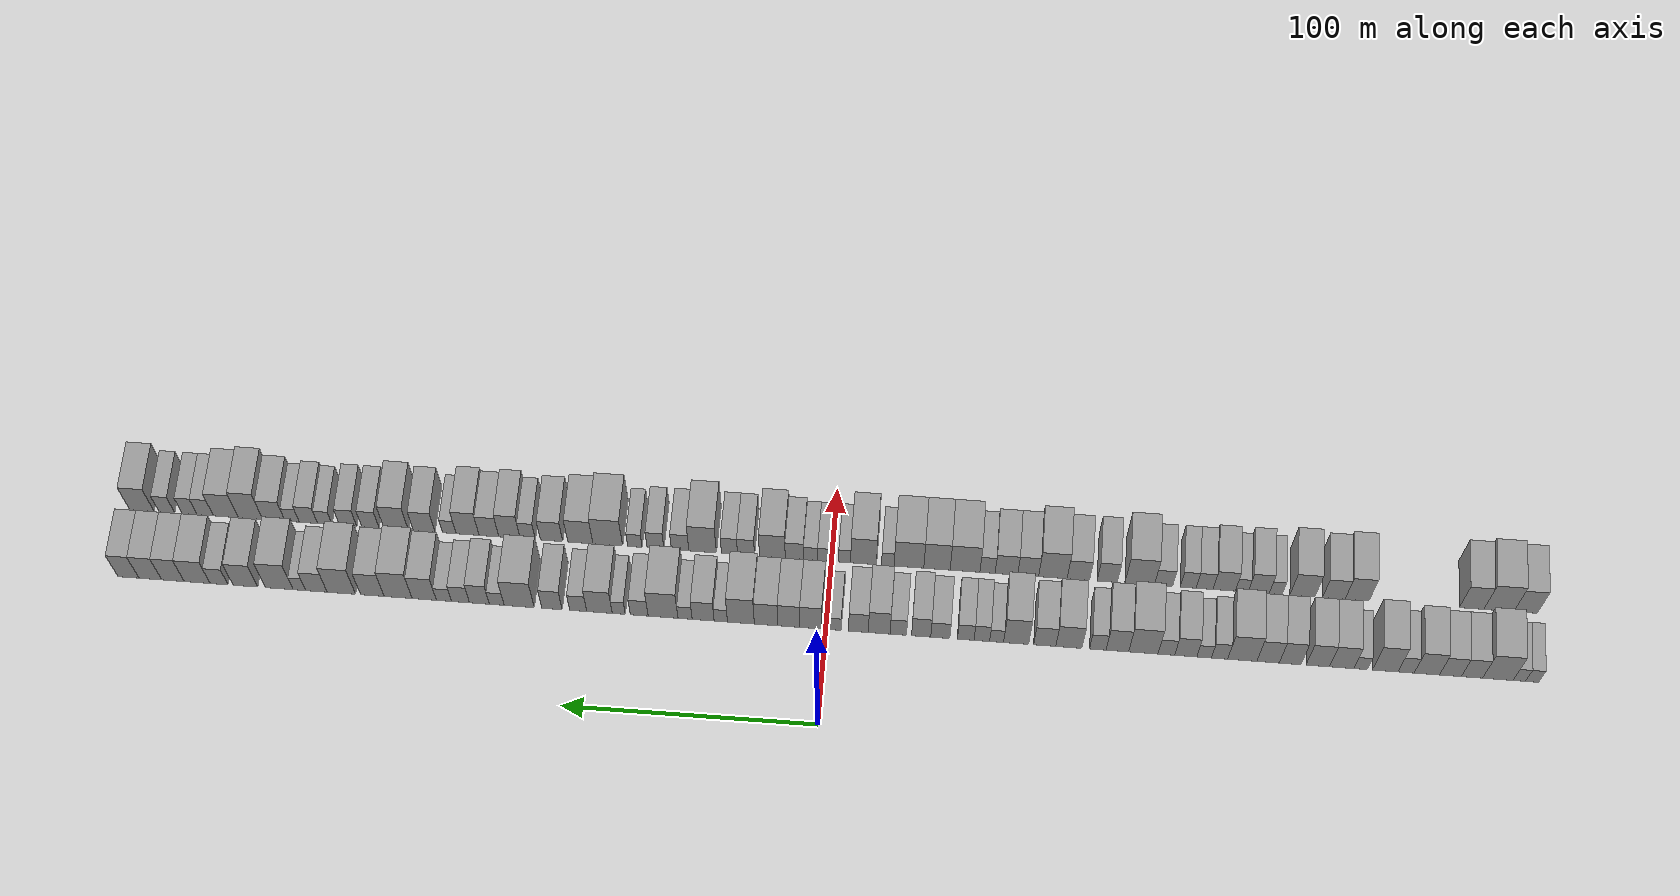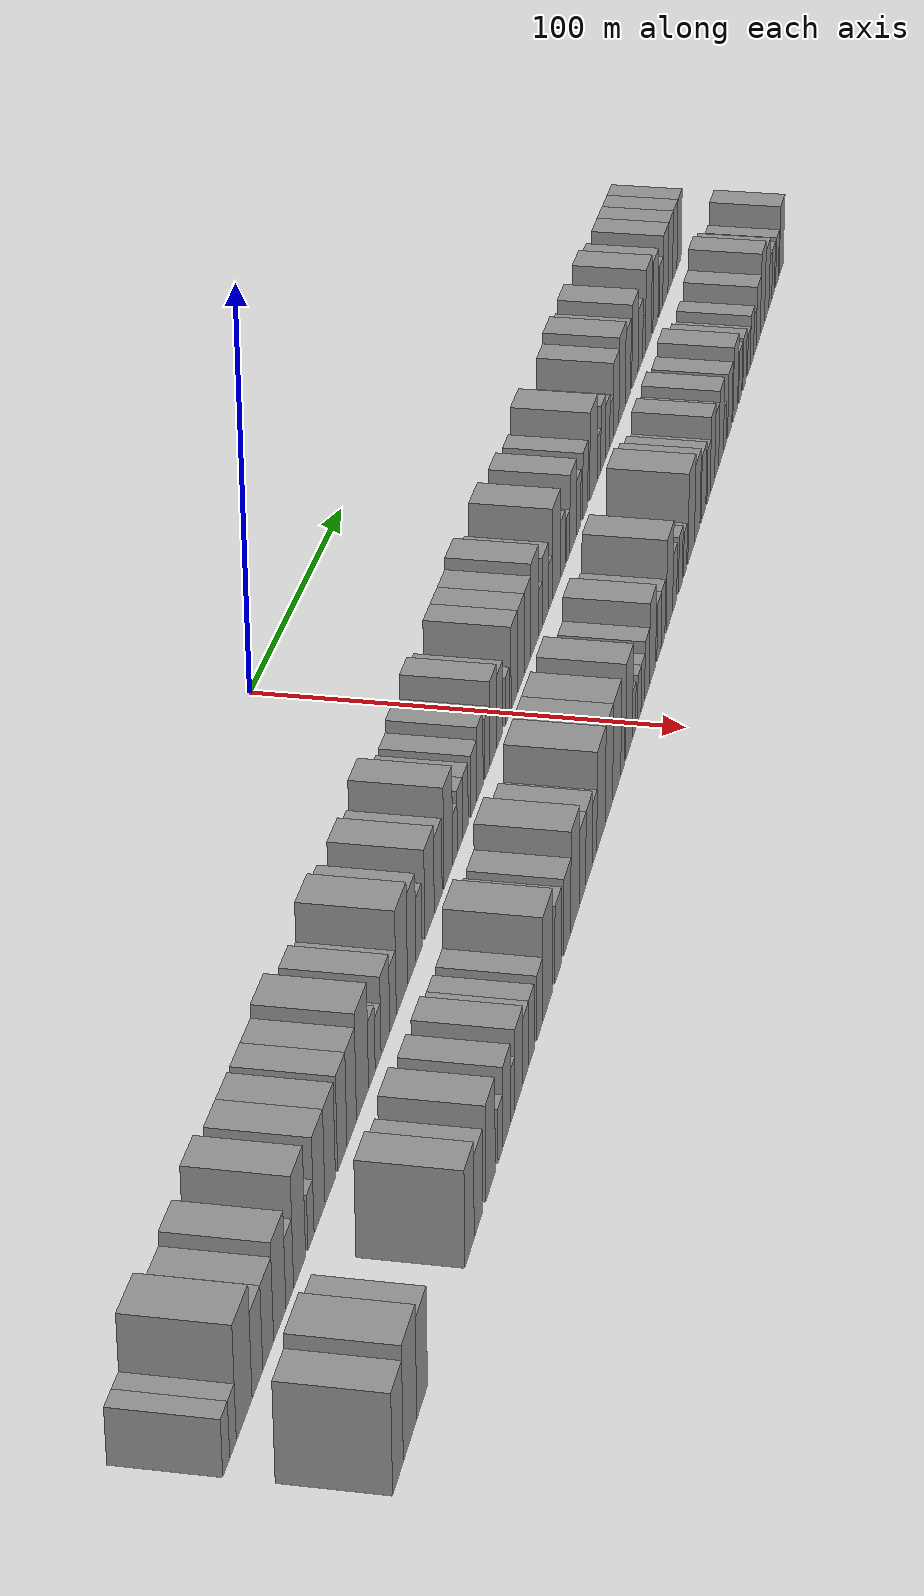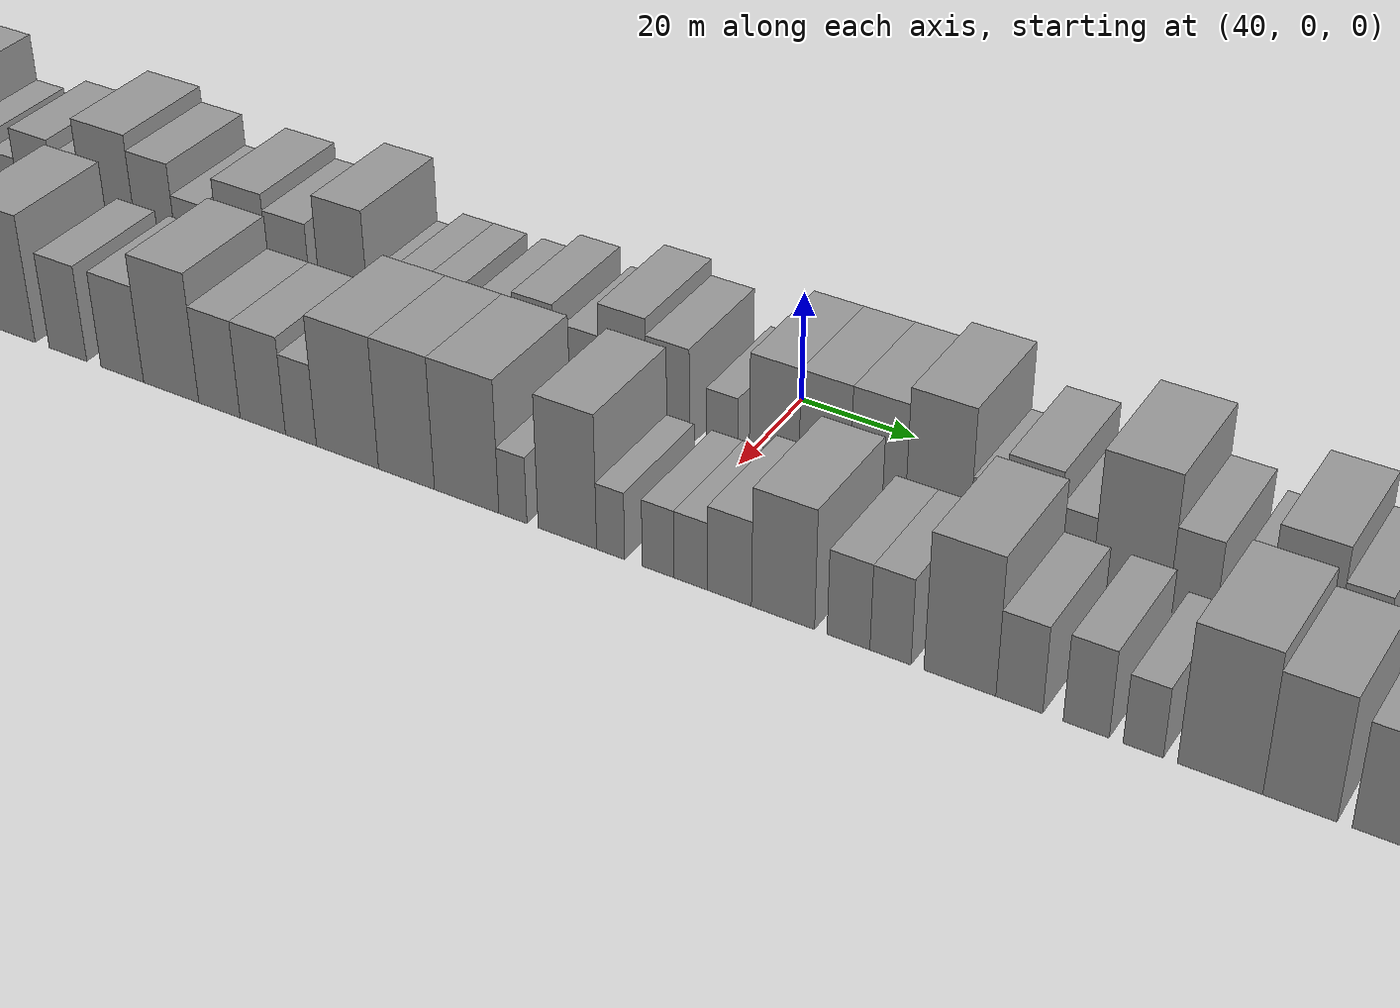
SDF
<sdf version="1.6">
 <world name="default">
  <scene>
   <sky><clouds><speed>12</speed></clouds></sky>
   <ambient>0.4 0.4 0.4 1</ambient>
   <background>0.7 0.7 0.7 1</background>
   <shadows>1</shadows>
  </scene>
  <gravity>0 0 -9.8066</gravity>
  <magnetic_field>6e-06 2.3e-05 -4.2e-05</magnetic_field>
  <physics default="0" name="default_physics" type="ode">
   <ode>
    <solver>
     <type>quick</type>
     <iters>10</iters>
     <sor>1.0</sor>
     <use_dynamic_moi_rescaling>0</use_dynamic_moi_rescaling>
    </solver>
    <constraints>
     <cfm>0</cfm>
     <erp>0.2</erp>
     <contact_max_correcting_vel>100</contact_max_correcting_vel>
     <contact_surface_layer>0.001</contact_surface_layer>
    </constraints>
   </ode>
   <max_step_size>0.004</max_step_size>
   <real_time_factor>1</real_time_factor>
   <real_time_update_rate>250</real_time_update_rate>
  </physics>
  <light name="sun" type="directional">
   <pose>0 0 10 0 0 0</pose>
   <diffuse>0.8 0.8 0.8 1</diffuse>
   <specular>0.2 0.2 0.2 1</specular>
   <attenuation>
    <range>1000</range>
    <constant>0.9</constant>
    <linear>0.01</linear>
    <quadratic>0.001</quadratic>
   </attenuation>
   <direction>-0.5 0.1 -0.9</direction>
  </light>
  <model name="building_1">
   <static>1</static>
   <pose>50.0000 -275.4501 0 0.000000 0.000000 0.000000</pose>
   <link name="link">
    <pose>0 0 6.00 0 0 0</pose>
    <collision name="collision"><geometry><box><size>20.0000 5.0997 12.0000</size></box></geometry></collision>
    <visual name="visual">
     <cast_shadows>0</cast_shadows>
     <geometry><box><size>20.0000 5.0997 12.0000</size></box></geometry>
     <material>
      <script>
       <uri>model://grey_wall/materials/scripts</uri>
       <uri>model://grey_wall/materials/textures</uri>
       <name>vrc/grey_wall</name>
      </script>
     </material>
    </visual>
   </link>
  </model>
  <model name="building_2">
   <static>1</static>
   <pose>50.0000 -270.4761 0 0.000000 0.000000 0.000000</pose>
   <link name="link">
    <pose>0 0 6.00 0 0 0</pose>
    <collision name="collision"><geometry><box><size>20.0000 4.8484 12.0000</size></box></geometry></collision>
    <visual name="visual">
     <cast_shadows>0</cast_shadows>
     <geometry><box><size>20.0000 4.8484 12.0000</size></box></geometry>
     <material>
      <script>
       <uri>model://grey_wall/materials/scripts</uri>
       <uri>model://grey_wall/materials/textures</uri>
       <name>vrc/grey_wall</name>
      </script>
     </material>
    </visual>
   </link>
  </model>
  <model name="building_3">
   <static>1</static>
   <pose>50.0000 -262.1490 0 0.000000 0.000000 0.000000</pose>
   <link name="link">
    <pose>0 0 12.00 0 0 0</pose>
    <collision name="collision"><geometry><box><size>20.0000 11.8057 24.0000</size></box></geometry></collision>
    <visual name="visual">
     <cast_shadows>0</cast_shadows>
     <geometry><box><size>20.0000 11.8057 24.0000</size></box></geometry>
     <material>
      <script>
       <uri>model://grey_wall/materials/scripts</uri>
       <uri>model://grey_wall/materials/textures</uri>
       <name>vrc/grey_wall</name>
      </script>
     </material>
    </visual>
   </link>
  </model>
  <model name="building_4">
   <static>1</static>
   <pose>50.0000 -252.1356 0 0.000000 0.000000 0.000000</pose>
   <link name="link">
    <pose>0 0 9.00 0 0 0</pose>
    <collision name="collision"><geometry><box><size>20.0000 8.2212 18.0000</size></box></geometry></collision>
    <visual name="visual">
     <cast_shadows>0</cast_shadows>
     <geometry><box><size>20.0000 8.2212 18.0000</size></box></geometry>
     <material>
      <script>
       <uri>model://grey_wall/materials/scripts</uri>
       <uri>model://grey_wall/materials/textures</uri>
       <name>vrc/grey_wall</name>
      </script>
     </material>
    </visual>
   </link>
  </model>
  <model name="building_5">
   <static>1</static>
   <pose>50.0000 -243.7747 0 0.000000 0.000000 0.000000</pose>
   <link name="link">
    <pose>0 0 9.00 0 0 0</pose>
    <collision name="collision"><geometry><box><size>20.0000 8.5006 18.0000</size></box></geometry></collision>
    <visual name="visual">
     <cast_shadows>0</cast_shadows>
     <geometry><box><size>20.0000 8.5006 18.0000</size></box></geometry>
     <material>
      <script>
       <uri>model://grey_wall/materials/scripts</uri>
       <uri>model://grey_wall/materials/textures</uri>
       <name>vrc/grey_wall</name>
      </script>
     </material>
    </visual>
   </link>
  </model>
  <model name="building_6">
   <static>1</static>
   <pose>50.0000 -234.6175 0 0.000000 0.000000 0.000000</pose>
   <link name="link">
    <pose>0 0 10.50 0 0 0</pose>
    <collision name="collision"><geometry><box><size>20.0000 9.8136 21.0000</size></box></geometry></collision>
    <visual name="visual">
     <cast_shadows>0</cast_shadows>
     <geometry><box><size>20.0000 9.8136 21.0000</size></box></geometry>
     <material>
      <script>
       <uri>model://grey_wall/materials/scripts</uri>
       <uri>model://grey_wall/materials/textures</uri>
       <name>vrc/grey_wall</name>
      </script>
     </material>
    </visual>
   </link>
  </model>
  <model name="building_7">
   <static>1</static>
   <pose>50.0000 -226.5610 0 0.000000 0.000000 0.000000</pose>
   <link name="link">
    <pose>0 0 7.50 0 0 0</pose>
    <collision name="collision"><geometry><box><size>20.0000 6.2995 15.0000</size></box></geometry></collision>
    <visual name="visual">
     <cast_shadows>0</cast_shadows>
     <geometry><box><size>20.0000 6.2995 15.0000</size></box></geometry>
     <material>
      <script>
       <uri>model://grey_wall/materials/scripts</uri>
       <uri>model://grey_wall/materials/textures</uri>
       <name>vrc/grey_wall</name>
      </script>
     </material>
    </visual>
   </link>
  </model>
  <model name="building_8">
   <static>1</static>
   <pose>50.0000 -218.4546 0 0.000000 0.000000 0.000000</pose>
   <link name="link">
    <pose>0 0 12.00 0 0 0</pose>
    <collision name="collision"><geometry><box><size>20.0000 9.9131 24.0000</size></box></geometry></collision>
    <visual name="visual">
     <cast_shadows>0</cast_shadows>
     <geometry><box><size>20.0000 9.9131 24.0000</size></box></geometry>
     <material>
      <script>
       <uri>model://grey_wall/materials/scripts</uri>
       <uri>model://grey_wall/materials/textures</uri>
       <name>vrc/grey_wall</name>
      </script>
     </material>
    </visual>
   </link>
  </model>
  <model name="building_9">
   <static>1</static>
   <pose>50.0000 -208.9025 0 0.000000 0.000000 0.000000</pose>
   <link name="link">
    <pose>0 0 6.00 0 0 0</pose>
    <collision name="collision"><geometry><box><size>20.0000 5.1912 12.0000</size></box></geometry></collision>
    <visual name="visual">
     <cast_shadows>0</cast_shadows>
     <geometry><box><size>20.0000 5.1912 12.0000</size></box></geometry>
     <material>
      <script>
       <uri>model://grey_wall/materials/scripts</uri>
       <uri>model://grey_wall/materials/textures</uri>
       <name>vrc/grey_wall</name>
      </script>
     </material>
    </visual>
   </link>
  </model>
  <model name="building_10">
   <static>1</static>
   <pose>50.0000 -201.5796 0 0.000000 0.000000 0.000000</pose>
   <link name="link">
    <pose>0 0 10.50 0 0 0</pose>
    <collision name="collision"><geometry><box><size>20.0000 9.4546 21.0000</size></box></geometry></collision>
    <visual name="visual">
     <cast_shadows>0</cast_shadows>
     <geometry><box><size>20.0000 9.4546 21.0000</size></box></geometry>
     <material>
      <script>
       <uri>model://grey_wall/materials/scripts</uri>
       <uri>model://grey_wall/materials/textures</uri>
       <name>vrc/grey_wall</name>
      </script>
     </material>
    </visual>
   </link>
  </model>
  <model name="building_11">
   <static>1</static>
   <pose>50.0000 -192.2869 0 0.000000 0.000000 0.000000</pose>
   <link name="link">
    <pose>0 0 10.50 0 0 0</pose>
    <collision name="collision"><geometry><box><size>20.0000 9.1308 21.0000</size></box></geometry></collision>
    <visual name="visual">
     <cast_shadows>0</cast_shadows>
     <geometry><box><size>20.0000 9.1308 21.0000</size></box></geometry>
     <material>
      <script>
       <uri>model://grey_wall/materials/scripts</uri>
       <uri>model://grey_wall/materials/textures</uri>
       <name>vrc/grey_wall</name>
      </script>
     </material>
    </visual>
   </link>
  </model>
  <model name="building_12">
   <static>1</static>
   <pose>50.0000 -181.5034 0 0.000000 0.000000 0.000000</pose>
   <link name="link">
    <pose>0 0 10.50 0 0 0</pose>
    <collision name="collision"><geometry><box><size>20.0000 8.4361 21.0000</size></box></geometry></collision>
    <visual name="visual">
     <cast_shadows>0</cast_shadows>
     <geometry><box><size>20.0000 8.4361 21.0000</size></box></geometry>
     <material>
      <script>
       <uri>model://grey_wall/materials/scripts</uri>
       <uri>model://grey_wall/materials/textures</uri>
       <name>vrc/grey_wall</name>
      </script>
     </material>
    </visual>
   </link>
  </model>
  <model name="building_13">
   <static>1</static>
   <pose>50.0000 -172.9142 0 0.000000 0.000000 0.000000</pose>
   <link name="link">
    <pose>0 0 10.50 0 0 0</pose>
    <collision name="collision"><geometry><box><size>20.0000 8.7424 21.0000</size></box></geometry></collision>
    <visual name="visual">
     <cast_shadows>0</cast_shadows>
     <geometry><box><size>20.0000 8.7424 21.0000</size></box></geometry>
     <material>
      <script>
       <uri>model://grey_wall/materials/scripts</uri>
       <uri>model://grey_wall/materials/textures</uri>
       <name>vrc/grey_wall</name>
      </script>
     </material>
    </visual>
   </link>
  </model>
  <model name="building_14">
   <static>1</static>
   <pose>50.0000 -162.8512 0 0.000000 0.000000 0.000000</pose>
   <link name="link">
    <pose>0 0 12.00 0 0 0</pose>
    <collision name="collision"><geometry><box><size>20.0000 11.3835 24.0000</size></box></geometry></collision>
    <visual name="visual">
     <cast_shadows>0</cast_shadows>
     <geometry><box><size>20.0000 11.3835 24.0000</size></box></geometry>
     <material>
      <script>
       <uri>model://grey_wall/materials/scripts</uri>
       <uri>model://grey_wall/materials/textures</uri>
       <name>vrc/grey_wall</name>
      </script>
     </material>
    </visual>
   </link>
  </model>
  <model name="building_15">
   <static>1</static>
   <pose>50.0000 -153.9894 0 0.000000 0.000000 0.000000</pose>
   <link name="link">
    <pose>0 0 7.50 0 0 0</pose>
    <collision name="collision"><geometry><box><size>20.0000 6.3402 15.0000</size></box></geometry></collision>
    <visual name="visual">
     <cast_shadows>0</cast_shadows>
     <geometry><box><size>20.0000 6.3402 15.0000</size></box></geometry>
     <material>
      <script>
       <uri>model://grey_wall/materials/scripts</uri>
       <uri>model://grey_wall/materials/textures</uri>
       <name>vrc/grey_wall</name>
      </script>
     </material>
    </visual>
   </link>
  </model>
  <model name="building_16">
   <static>1</static>
   <pose>50.0000 -147.9651 0 0.000000 0.000000 0.000000</pose>
   <link name="link">
    <pose>0 0 6.00 0 0 0</pose>
    <collision name="collision"><geometry><box><size>20.0000 5.7084 12.0000</size></box></geometry></collision>
    <visual name="visual">
     <cast_shadows>0</cast_shadows>
     <geometry><box><size>20.0000 5.7084 12.0000</size></box></geometry>
     <material>
      <script>
       <uri>model://grey_wall/materials/scripts</uri>
       <uri>model://grey_wall/materials/textures</uri>
       <name>vrc/grey_wall</name>
      </script>
     </material>
    </visual>
   </link>
  </model>
  <model name="building_17">
   <static>1</static>
   <pose>50.0000 -140.8006 0 0.000000 0.000000 0.000000</pose>
   <link name="link">
    <pose>0 0 9.00 0 0 0</pose>
    <collision name="collision"><geometry><box><size>20.0000 8.6206 18.0000</size></box></geometry></collision>
    <visual name="visual">
     <cast_shadows>0</cast_shadows>
     <geometry><box><size>20.0000 8.6206 18.0000</size></box></geometry>
     <material>
      <script>
       <uri>model://grey_wall/materials/scripts</uri>
       <uri>model://grey_wall/materials/textures</uri>
       <name>vrc/grey_wall</name>
      </script>
     </material>
    </visual>
   </link>
  </model>
  <model name="building_18">
   <static>1</static>
   <pose>50.0000 -133.2432 0 0.000000 0.000000 0.000000</pose>
   <link name="link">
    <pose>0 0 7.50 0 0 0</pose>
    <collision name="collision"><geometry><box><size>20.0000 6.4942 15.0000</size></box></geometry></collision>
    <visual name="visual">
     <cast_shadows>0</cast_shadows>
     <geometry><box><size>20.0000 6.4942 15.0000</size></box></geometry>
     <material>
      <script>
       <uri>model://grey_wall/materials/scripts</uri>
       <uri>model://grey_wall/materials/textures</uri>
       <name>vrc/grey_wall</name>
      </script>
     </material>
    </visual>
   </link>
  </model>
  <model name="building_19">
   <static>1</static>
   <pose>50.0000 -124.2672 0 0.000000 0.000000 0.000000</pose>
   <link name="link">
    <pose>0 0 12.00 0 0 0</pose>
    <collision name="collision"><geometry><box><size>20.0000 11.4578 24.0000</size></box></geometry></collision>
    <visual name="visual">
     <cast_shadows>0</cast_shadows>
     <geometry><box><size>20.0000 11.4578 24.0000</size></box></geometry>
     <material>
      <script>
       <uri>model://grey_wall/materials/scripts</uri>
       <uri>model://grey_wall/materials/textures</uri>
       <name>vrc/grey_wall</name>
      </script>
     </material>
    </visual>
   </link>
  </model>
  <model name="building_20">
   <static>1</static>
   <pose>50.0000 -114.1282 0 0.000000 0.000000 0.000000</pose>
   <link name="link">
    <pose>0 0 10.50 0 0 0</pose>
    <collision name="collision"><geometry><box><size>20.0000 8.8202 21.0000</size></box></geometry></collision>
    <visual name="visual">
     <cast_shadows>0</cast_shadows>
     <geometry><box><size>20.0000 8.8202 21.0000</size></box></geometry>
     <material>
      <script>
       <uri>model://grey_wall/materials/scripts</uri>
       <uri>model://grey_wall/materials/textures</uri>
       <name>vrc/grey_wall</name>
      </script>
     </material>
    </visual>
   </link>
  </model>
  <model name="building_21">
   <static>1</static>
   <pose>50.0000 -106.4901 0 0.000000 0.000000 0.000000</pose>
   <link name="link">
    <pose>0 0 7.50 0 0 0</pose>
    <collision name="collision"><geometry><box><size>20.0000 6.4560 15.0000</size></box></geometry></collision>
    <visual name="visual">
     <cast_shadows>0</cast_shadows>
     <geometry><box><size>20.0000 6.4560 15.0000</size></box></geometry>
     <material>
      <script>
       <uri>model://grey_wall/materials/scripts</uri>
       <uri>model://grey_wall/materials/textures</uri>
       <name>vrc/grey_wall</name>
      </script>
     </material>
    </visual>
   </link>
  </model>
  <model name="building_22">
   <static>1</static>
   <pose>50.0000 -95.1648 0 0.000000 0.000000 0.000000</pose>
   <link name="link">
    <pose>0 0 10.50 0 0 0</pose>
    <collision name="collision"><geometry><box><size>20.0000 10.1945 21.0000</size></box></geometry></collision>
    <visual name="visual">
     <cast_shadows>0</cast_shadows>
     <geometry><box><size>20.0000 10.1945 21.0000</size></box></geometry>
     <material>
      <script>
       <uri>model://grey_wall/materials/scripts</uri>
       <uri>model://grey_wall/materials/textures</uri>
       <name>vrc/grey_wall</name>
      </script>
     </material>
    </visual>
   </link>
  </model>
  <model name="building_23">
   <static>1</static>
   <pose>50.0000 -85.7402 0 0.000000 0.000000 0.000000</pose>
   <link name="link">
    <pose>0 0 9.00 0 0 0</pose>
    <collision name="collision"><geometry><box><size>20.0000 8.6548 18.0000</size></box></geometry></collision>
    <visual name="visual">
     <cast_shadows>0</cast_shadows>
     <geometry><box><size>20.0000 8.6548 18.0000</size></box></geometry>
     <material>
      <script>
       <uri>model://grey_wall/materials/scripts</uri>
       <uri>model://grey_wall/materials/textures</uri>
       <name>vrc/grey_wall</name>
      </script>
     </material>
    </visual>
   </link>
  </model>
  <model name="building_24">
   <static>1</static>
   <pose>50.0000 -74.5059 0 0.000000 0.000000 0.000000</pose>
   <link name="link">
    <pose>0 0 12.00 0 0 0</pose>
    <collision name="collision"><geometry><box><size>20.0000 9.8138 24.0000</size></box></geometry></collision>
    <visual name="visual">
     <cast_shadows>0</cast_shadows>
     <geometry><box><size>20.0000 9.8138 24.0000</size></box></geometry>
     <material>
      <script>
       <uri>model://grey_wall/materials/scripts</uri>
       <uri>model://grey_wall/materials/textures</uri>
       <name>vrc/grey_wall</name>
      </script>
     </material>
    </visual>
   </link>
  </model>
  <model name="building_25">
   <static>1</static>
   <pose>50.0000 -66.8826 0 0.000000 0.000000 0.000000</pose>
   <link name="link">
    <pose>0 0 6.00 0 0 0</pose>
    <collision name="collision"><geometry><box><size>20.0000 5.4328 12.0000</size></box></geometry></collision>
    <visual name="visual">
     <cast_shadows>0</cast_shadows>
     <geometry><box><size>20.0000 5.4328 12.0000</size></box></geometry>
     <material>
      <script>
       <uri>model://grey_wall/materials/scripts</uri>
       <uri>model://grey_wall/materials/textures</uri>
       <name>vrc/grey_wall</name>
      </script>
     </material>
    </visual>
   </link>
  </model>
  <model name="building_26">
   <static>1</static>
   <pose>50.0000 -61.1020 0 0.000000 0.000000 0.000000</pose>
   <link name="link">
    <pose>0 0 7.50 0 0 0</pose>
    <collision name="collision"><geometry><box><size>20.0000 6.1285 15.0000</size></box></geometry></collision>
    <visual name="visual">
     <cast_shadows>0</cast_shadows>
     <geometry><box><size>20.0000 6.1285 15.0000</size></box></geometry>
     <material>
      <script>
       <uri>model://grey_wall/materials/scripts</uri>
       <uri>model://grey_wall/materials/textures</uri>
       <name>vrc/grey_wall</name>
      </script>
     </material>
    </visual>
   </link>
  </model>
  <model name="building_27">
   <static>1</static>
   <pose>50.0000 -54.7877 0 0.000000 0.000000 0.000000</pose>
   <link name="link">
    <pose>0 0 7.50 0 0 0</pose>
    <collision name="collision"><geometry><box><size>20.0000 6.5000 15.0000</size></box></geometry></collision>
    <visual name="visual">
     <cast_shadows>0</cast_shadows>
     <geometry><box><size>20.0000 6.5000 15.0000</size></box></geometry>
     <material>
      <script>
       <uri>model://grey_wall/materials/scripts</uri>
       <uri>model://grey_wall/materials/textures</uri>
       <name>vrc/grey_wall</name>
      </script>
     </material>
    </visual>
   </link>
  </model>
  <model name="building_28">
   <static>1</static>
   <pose>50.0000 -44.8088 0 0.000000 0.000000 0.000000</pose>
   <link name="link">
    <pose>0 0 7.50 0 0 0</pose>
    <collision name="collision"><geometry><box><size>20.0000 7.4579 15.0000</size></box></geometry></collision>
    <visual name="visual">
     <cast_shadows>0</cast_shadows>
     <geometry><box><size>20.0000 7.4579 15.0000</size></box></geometry>
     <material>
      <script>
       <uri>model://grey_wall/materials/scripts</uri>
       <uri>model://grey_wall/materials/textures</uri>
       <name>vrc/grey_wall</name>
      </script>
     </material>
    </visual>
   </link>
  </model>
  <model name="building_29">
   <static>1</static>
   <pose>50.0000 -37.3295 0 0.000000 0.000000 0.000000</pose>
   <link name="link">
    <pose>0 0 9.00 0 0 0</pose>
    <collision name="collision"><geometry><box><size>20.0000 7.5007 18.0000</size></box></geometry></collision>
    <visual name="visual">
     <cast_shadows>0</cast_shadows>
     <geometry><box><size>20.0000 7.5007 18.0000</size></box></geometry>
     <material>
      <script>
       <uri>model://grey_wall/materials/scripts</uri>
       <uri>model://grey_wall/materials/textures</uri>
       <name>vrc/grey_wall</name>
      </script>
     </material>
    </visual>
   </link>
  </model>
  <model name="building_30">
   <static>1</static>
   <pose>50.0000 -28.3848 0 0.000000 0.000000 0.000000</pose>
   <link name="link">
    <pose>0 0 7.50 0 0 0</pose>
    <collision name="collision"><geometry><box><size>20.0000 6.3886 15.0000</size></box></geometry></collision>
    <visual name="visual">
     <cast_shadows>0</cast_shadows>
     <geometry><box><size>20.0000 6.3886 15.0000</size></box></geometry>
     <material>
      <script>
       <uri>model://grey_wall/materials/scripts</uri>
       <uri>model://grey_wall/materials/textures</uri>
       <name>vrc/grey_wall</name>
      </script>
     </material>
    </visual>
   </link>
  </model>
  <model name="building_31">
   <static>1</static>
   <pose>50.0000 -20.9215 0 0.000000 0.000000 0.000000</pose>
   <link name="link">
    <pose>0 0 10.50 0 0 0</pose>
    <collision name="collision"><geometry><box><size>20.0000 8.5380 21.0000</size></box></geometry></collision>
    <visual name="visual">
     <cast_shadows>0</cast_shadows>
     <geometry><box><size>20.0000 8.5380 21.0000</size></box></geometry>
     <material>
      <script>
       <uri>model://grey_wall/materials/scripts</uri>
       <uri>model://grey_wall/materials/textures</uri>
       <name>vrc/grey_wall</name>
      </script>
     </material>
    </visual>
   </link>
  </model>
  <model name="building_32">
   <static>1</static>
   <pose>50.0000 -12.7740 0 0.000000 0.000000 0.000000</pose>
   <link name="link">
    <pose>0 0 9.00 0 0 0</pose>
    <collision name="collision"><geometry><box><size>20.0000 7.7571 18.0000</size></box></geometry></collision>
    <visual name="visual">
     <cast_shadows>0</cast_shadows>
     <geometry><box><size>20.0000 7.7571 18.0000</size></box></geometry>
     <material>
      <script>
       <uri>model://grey_wall/materials/scripts</uri>
       <uri>model://grey_wall/materials/textures</uri>
       <name>vrc/grey_wall</name>
      </script>
     </material>
    </visual>
   </link>
  </model>
  <model name="building_33">
   <static>1</static>
   <pose>50.0000 -3.0939 0 0.000000 0.000000 0.000000</pose>
   <link name="link">
    <pose>0 0 6.00 0 0 0</pose>
    <collision name="collision"><geometry><box><size>20.0000 5.6031 12.0000</size></box></geometry></collision>
    <visual name="visual">
     <cast_shadows>0</cast_shadows>
     <geometry><box><size>20.0000 5.6031 12.0000</size></box></geometry>
     <material>
      <script>
       <uri>model://grey_wall/materials/scripts</uri>
       <uri>model://grey_wall/materials/textures</uri>
       <name>vrc/grey_wall</name>
      </script>
     </material>
    </visual>
   </link>
  </model>
  <model name="building_34">
   <static>1</static>
   <pose>50.0000 5.9939 0 0.000000 0.000000 0.000000</pose>
   <link name="link">
    <pose>0 0 10.50 0 0 0</pose>
    <collision name="collision"><geometry><box><size>20.0000 8.5725 21.0000</size></box></geometry></collision>
    <visual name="visual">
     <cast_shadows>0</cast_shadows>
     <geometry><box><size>20.0000 8.5725 21.0000</size></box></geometry>
     <material>
      <script>
       <uri>model://grey_wall/materials/scripts</uri>
       <uri>model://grey_wall/materials/textures</uri>
       <name>vrc/grey_wall</name>
      </script>
     </material>
    </visual>
   </link>
  </model>
  <model name="building_35">
   <static>1</static>
   <pose>50.0000 14.6316 0 0.000000 0.000000 0.000000</pose>
   <link name="link">
    <pose>0 0 10.50 0 0 0</pose>
    <collision name="collision"><geometry><box><size>20.0000 8.7028 21.0000</size></box></geometry></collision>
    <visual name="visual">
     <cast_shadows>0</cast_shadows>
     <geometry><box><size>20.0000 8.7028 21.0000</size></box></geometry>
     <material>
      <script>
       <uri>model://grey_wall/materials/scripts</uri>
       <uri>model://grey_wall/materials/textures</uri>
       <name>vrc/grey_wall</name>
      </script>
     </material>
    </visual>
   </link>
  </model>
  <model name="building_36">
   <static>1</static>
   <pose>50.0000 23.6154 0 0.000000 0.000000 0.000000</pose>
   <link name="link">
    <pose>0 0 10.50 0 0 0</pose>
    <collision name="collision"><geometry><box><size>20.0000 9.2649 21.0000</size></box></geometry></collision>
    <visual name="visual">
     <cast_shadows>0</cast_shadows>
     <geometry><box><size>20.0000 9.2649 21.0000</size></box></geometry>
     <material>
      <script>
       <uri>model://grey_wall/materials/scripts</uri>
       <uri>model://grey_wall/materials/textures</uri>
       <name>vrc/grey_wall</name>
      </script>
     </material>
    </visual>
   </link>
  </model>
  <model name="building_37">
   <static>1</static>
   <pose>50.0000 33.5386 0 0.000000 0.000000 0.000000</pose>
   <link name="link">
    <pose>0 0 12.00 0 0 0</pose>
    <collision name="collision"><geometry><box><size>20.0000 10.5815 24.0000</size></box></geometry></collision>
    <visual name="visual">
     <cast_shadows>0</cast_shadows>
     <geometry><box><size>20.0000 10.5815 24.0000</size></box></geometry>
     <material>
      <script>
       <uri>model://grey_wall/materials/scripts</uri>
       <uri>model://grey_wall/materials/textures</uri>
       <name>vrc/grey_wall</name>
      </script>
     </material>
    </visual>
   </link>
  </model>
  <model name="building_38">
   <static>1</static>
   <pose>50.0000 41.4496 0 0.000000 0.000000 0.000000</pose>
   <link name="link">
    <pose>0 0 6.00 0 0 0</pose>
    <collision name="collision"><geometry><box><size>20.0000 5.2403 12.0000</size></box></geometry></collision>
    <visual name="visual">
     <cast_shadows>0</cast_shadows>
     <geometry><box><size>20.0000 5.2403 12.0000</size></box></geometry>
     <material>
      <script>
       <uri>model://grey_wall/materials/scripts</uri>
       <uri>model://grey_wall/materials/textures</uri>
       <name>vrc/grey_wall</name>
      </script>
     </material>
    </visual>
   </link>
  </model>
  <model name="building_39">
   <static>1</static>
   <pose>50.0000 48.4071 0 0.000000 0.000000 0.000000</pose>
   <link name="link">
    <pose>0 0 9.00 0 0 0</pose>
    <collision name="collision"><geometry><box><size>20.0000 8.6749 18.0000</size></box></geometry></collision>
    <visual name="visual">
     <cast_shadows>0</cast_shadows>
     <geometry><box><size>20.0000 8.6749 18.0000</size></box></geometry>
     <material>
      <script>
       <uri>model://grey_wall/materials/scripts</uri>
       <uri>model://grey_wall/materials/textures</uri>
       <name>vrc/grey_wall</name>
      </script>
     </material>
    </visual>
   </link>
  </model>
  <model name="building_40">
   <static>1</static>
   <pose>50.0000 55.5318 0 0.000000 0.000000 0.000000</pose>
   <link name="link">
    <pose>0 0 6.00 0 0 0</pose>
    <collision name="collision"><geometry><box><size>20.0000 5.5745 12.0000</size></box></geometry></collision>
    <visual name="visual">
     <cast_shadows>0</cast_shadows>
     <geometry><box><size>20.0000 5.5745 12.0000</size></box></geometry>
     <material>
      <script>
       <uri>model://grey_wall/materials/scripts</uri>
       <uri>model://grey_wall/materials/textures</uri>
       <name>vrc/grey_wall</name>
      </script>
     </material>
    </visual>
   </link>
  </model>
  <model name="building_41">
   <static>1</static>
   <pose>50.0000 64.1976 0 0.000000 0.000000 0.000000</pose>
   <link name="link">
    <pose>0 0 12.00 0 0 0</pose>
    <collision name="collision"><geometry><box><size>20.0000 11.7571 24.0000</size></box></geometry></collision>
    <visual name="visual">
     <cast_shadows>0</cast_shadows>
     <geometry><box><size>20.0000 11.7571 24.0000</size></box></geometry>
     <material>
      <script>
       <uri>model://grey_wall/materials/scripts</uri>
       <uri>model://grey_wall/materials/textures</uri>
       <name>vrc/grey_wall</name>
      </script>
     </material>
    </visual>
   </link>
  </model>
  <model name="building_42">
   <static>1</static>
   <pose>50.0000 73.5906 0 0.000000 0.000000 0.000000</pose>
   <link name="link">
    <pose>0 0 7.50 0 0 0</pose>
    <collision name="collision"><geometry><box><size>20.0000 7.0291 15.0000</size></box></geometry></collision>
    <visual name="visual">
     <cast_shadows>0</cast_shadows>
     <geometry><box><size>20.0000 7.0291 15.0000</size></box></geometry>
     <material>
      <script>
       <uri>model://grey_wall/materials/scripts</uri>
       <uri>model://grey_wall/materials/textures</uri>
       <name>vrc/grey_wall</name>
      </script>
     </material>
    </visual>
   </link>
  </model>
  <model name="building_43">
   <static>1</static>
   <pose>50.0000 81.6611 0 0.000000 0.000000 0.000000</pose>
   <link name="link">
    <pose>0 0 6.00 0 0 0</pose>
    <collision name="collision"><geometry><box><size>20.0000 5.1118 12.0000</size></box></geometry></collision>
    <visual name="visual">
     <cast_shadows>0</cast_shadows>
     <geometry><box><size>20.0000 5.1118 12.0000</size></box></geometry>
     <material>
      <script>
       <uri>model://grey_wall/materials/scripts</uri>
       <uri>model://grey_wall/materials/textures</uri>
       <name>vrc/grey_wall</name>
      </script>
     </material>
    </visual>
   </link>
  </model>
  <model name="building_44">
   <static>1</static>
   <pose>50.0000 89.2601 0 0.000000 0.000000 0.000000</pose>
   <link name="link">
    <pose>0 0 10.50 0 0 0</pose>
    <collision name="collision"><geometry><box><size>20.0000 10.0862 21.0000</size></box></geometry></collision>
    <visual name="visual">
     <cast_shadows>0</cast_shadows>
     <geometry><box><size>20.0000 10.0862 21.0000</size></box></geometry>
     <material>
      <script>
       <uri>model://grey_wall/materials/scripts</uri>
       <uri>model://grey_wall/materials/textures</uri>
       <name>vrc/grey_wall</name>
      </script>
     </material>
    </visual>
   </link>
  </model>
  <model name="building_45">
   <static>1</static>
   <pose>50.0000 97.6707 0 0.000000 0.000000 0.000000</pose>
   <link name="link">
    <pose>0 0 7.50 0 0 0</pose>
    <collision name="collision"><geometry><box><size>20.0000 6.7349 15.0000</size></box></geometry></collision>
    <visual name="visual">
     <cast_shadows>0</cast_shadows>
     <geometry><box><size>20.0000 6.7349 15.0000</size></box></geometry>
     <material>
      <script>
       <uri>model://grey_wall/materials/scripts</uri>
       <uri>model://grey_wall/materials/textures</uri>
       <name>vrc/grey_wall</name>
      </script>
     </material>
    </visual>
   </link>
  </model>
  <model name="building_46">
   <static>1</static>
   <pose>50.0000 108.0494 0 0.000000 0.000000 0.000000</pose>
   <link name="link">
    <pose>0 0 9.00 0 0 0</pose>
    <collision name="collision"><geometry><box><size>20.0000 8.0226 18.0000</size></box></geometry></collision>
    <visual name="visual">
     <cast_shadows>0</cast_shadows>
     <geometry><box><size>20.0000 8.0226 18.0000</size></box></geometry>
     <material>
      <script>
       <uri>model://grey_wall/materials/scripts</uri>
       <uri>model://grey_wall/materials/textures</uri>
       <name>vrc/grey_wall</name>
      </script>
     </material>
    </visual>
   </link>
  </model>
  <model name="building_47">
   <static>1</static>
   <pose>50.0000 121.0334 0 0.000000 0.000000 0.000000</pose>
   <link name="link">
    <pose>0 0 12.00 0 0 0</pose>
    <collision name="collision"><geometry><box><size>20.0000 11.9454 24.0000</size></box></geometry></collision>
    <visual name="visual">
     <cast_shadows>0</cast_shadows>
     <geometry><box><size>20.0000 11.9454 24.0000</size></box></geometry>
     <material>
      <script>
       <uri>model://grey_wall/materials/scripts</uri>
       <uri>model://grey_wall/materials/textures</uri>
       <name>vrc/grey_wall</name>
      </script>
     </material>
    </visual>
   </link>
  </model>
  <model name="building_48">
   <static>1</static>
   <pose>50.0000 129.9564 0 0.000000 0.000000 0.000000</pose>
   <link name="link">
    <pose>0 0 6.00 0 0 0</pose>
    <collision name="collision"><geometry><box><size>20.0000 5.9007 12.0000</size></box></geometry></collision>
    <visual name="visual">
     <cast_shadows>0</cast_shadows>
     <geometry><box><size>20.0000 5.9007 12.0000</size></box></geometry>
     <material>
      <script>
       <uri>model://grey_wall/materials/scripts</uri>
       <uri>model://grey_wall/materials/textures</uri>
       <name>vrc/grey_wall</name>
      </script>
     </material>
    </visual>
   </link>
  </model>
  <model name="building_49">
   <static>1</static>
   <pose>50.0000 136.8345 0 0.000000 0.000000 0.000000</pose>
   <link name="link">
    <pose>0 0 9.00 0 0 0</pose>
    <collision name="collision"><geometry><box><size>20.0000 7.8554 18.0000</size></box></geometry></collision>
    <visual name="visual">
     <cast_shadows>0</cast_shadows>
     <geometry><box><size>20.0000 7.8554 18.0000</size></box></geometry>
     <material>
      <script>
       <uri>model://grey_wall/materials/scripts</uri>
       <uri>model://grey_wall/materials/textures</uri>
       <name>vrc/grey_wall</name>
      </script>
     </material>
    </visual>
   </link>
  </model>
  <model name="building_50">
   <static>1</static>
   <pose>50.0000 144.3161 0 0.000000 0.000000 0.000000</pose>
   <link name="link">
    <pose>0 0 7.50 0 0 0</pose>
    <collision name="collision"><geometry><box><size>20.0000 7.1079 15.0000</size></box></geometry></collision>
    <visual name="visual">
     <cast_shadows>0</cast_shadows>
     <geometry><box><size>20.0000 7.1079 15.0000</size></box></geometry>
     <material>
      <script>
       <uri>model://grey_wall/materials/scripts</uri>
       <uri>model://grey_wall/materials/textures</uri>
       <name>vrc/grey_wall</name>
      </script>
     </material>
    </visual>
   </link>
  </model>
  <model name="building_51">
   <static>1</static>
   <pose>50.0000 150.8622 0 0.000000 0.000000 0.000000</pose>
   <link name="link">
    <pose>0 0 6.00 0 0 0</pose>
    <collision name="collision"><geometry><box><size>20.0000 5.9843 12.0000</size></box></geometry></collision>
    <visual name="visual">
     <cast_shadows>0</cast_shadows>
     <geometry><box><size>20.0000 5.9843 12.0000</size></box></geometry>
     <material>
      <script>
       <uri>model://grey_wall/materials/scripts</uri>
       <uri>model://grey_wall/materials/textures</uri>
       <name>vrc/grey_wall</name>
      </script>
     </material>
    </visual>
   </link>
  </model>
  <model name="building_52">
   <static>1</static>
   <pose>50.0000 158.6646 0 0.000000 0.000000 0.000000</pose>
   <link name="link">
    <pose>0 0 10.50 0 0 0</pose>
    <collision name="collision"><geometry><box><size>20.0000 9.6206 21.0000</size></box></geometry></collision>
    <visual name="visual">
     <cast_shadows>0</cast_shadows>
     <geometry><box><size>20.0000 9.6206 21.0000</size></box></geometry>
     <material>
      <script>
       <uri>model://grey_wall/materials/scripts</uri>
       <uri>model://grey_wall/materials/textures</uri>
       <name>vrc/grey_wall</name>
      </script>
     </material>
    </visual>
   </link>
  </model>
  <model name="building_53">
   <static>1</static>
   <pose>50.0000 169.0447 0 0.000000 0.000000 0.000000</pose>
   <link name="link">
    <pose>0 0 12.00 0 0 0</pose>
    <collision name="collision"><geometry><box><size>20.0000 11.1397 24.0000</size></box></geometry></collision>
    <visual name="visual">
     <cast_shadows>0</cast_shadows>
     <geometry><box><size>20.0000 11.1397 24.0000</size></box></geometry>
     <material>
      <script>
       <uri>model://grey_wall/materials/scripts</uri>
       <uri>model://grey_wall/materials/textures</uri>
       <name>vrc/grey_wall</name>
      </script>
     </material>
    </visual>
   </link>
  </model>
  <model name="building_54">
   <static>1</static>
   <pose>50.0000 179.2855 0 0.000000 0.000000 0.000000</pose>
   <link name="link">
    <pose>0 0 10.50 0 0 0</pose>
    <collision name="collision"><geometry><box><size>20.0000 9.3417 21.0000</size></box></geometry></collision>
    <visual name="visual">
     <cast_shadows>0</cast_shadows>
     <geometry><box><size>20.0000 9.3417 21.0000</size></box></geometry>
     <material>
      <script>
       <uri>model://grey_wall/materials/scripts</uri>
       <uri>model://grey_wall/materials/textures</uri>
       <name>vrc/grey_wall</name>
      </script>
     </material>
    </visual>
   </link>
  </model>
  <model name="building_55">
   <static>1</static>
   <pose>50.0000 191.6050 0 0.000000 0.000000 0.000000</pose>
   <link name="link">
    <pose>0 0 12.00 0 0 0</pose>
    <collision name="collision"><geometry><box><size>20.0000 11.2973 24.0000</size></box></geometry></collision>
    <visual name="visual">
     <cast_shadows>0</cast_shadows>
     <geometry><box><size>20.0000 11.2973 24.0000</size></box></geometry>
     <material>
      <script>
       <uri>model://grey_wall/materials/scripts</uri>
       <uri>model://grey_wall/materials/textures</uri>
       <name>vrc/grey_wall</name>
      </script>
     </material>
    </visual>
   </link>
  </model>
  <model name="building_56">
   <static>1</static>
   <pose>50.0000 201.5154 0 0.000000 0.000000 0.000000</pose>
   <link name="link">
    <pose>0 0 9.00 0 0 0</pose>
    <collision name="collision"><geometry><box><size>20.0000 8.5236 18.0000</size></box></geometry></collision>
    <visual name="visual">
     <cast_shadows>0</cast_shadows>
     <geometry><box><size>20.0000 8.5236 18.0000</size></box></geometry>
     <material>
      <script>
       <uri>model://grey_wall/materials/scripts</uri>
       <uri>model://grey_wall/materials/textures</uri>
       <name>vrc/grey_wall</name>
      </script>
     </material>
    </visual>
   </link>
  </model>
  <model name="building_57">
   <static>1</static>
   <pose>50.0000 208.2696 0 0.000000 0.000000 0.000000</pose>
   <link name="link">
    <pose>0 0 6.00 0 0 0</pose>
    <collision name="collision"><geometry><box><size>20.0000 4.9847 12.0000</size></box></geometry></collision>
    <visual name="visual">
     <cast_shadows>0</cast_shadows>
     <geometry><box><size>20.0000 4.9847 12.0000</size></box></geometry>
     <material>
      <script>
       <uri>model://grey_wall/materials/scripts</uri>
       <uri>model://grey_wall/materials/textures</uri>
       <name>vrc/grey_wall</name>
      </script>
     </material>
    </visual>
   </link>
  </model>
  <model name="building_58">
   <static>1</static>
   <pose>50.0000 216.3229 0 0.000000 0.000000 0.000000</pose>
   <link name="link">
    <pose>0 0 12.00 0 0 0</pose>
    <collision name="collision"><geometry><box><size>20.0000 11.1220 24.0000</size></box></geometry></collision>
    <visual name="visual">
     <cast_shadows>0</cast_shadows>
     <geometry><box><size>20.0000 11.1220 24.0000</size></box></geometry>
     <material>
      <script>
       <uri>model://grey_wall/materials/scripts</uri>
       <uri>model://grey_wall/materials/textures</uri>
       <name>vrc/grey_wall</name>
      </script>
     </material>
    </visual>
   </link>
  </model>
  <model name="building_59">
   <static>1</static>
   <pose>50.0000 229.7855 0 0.000000 0.000000 0.000000</pose>
   <link name="link">
    <pose>0 0 10.50 0 0 0</pose>
    <collision name="collision"><geometry><box><size>20.0000 9.8032 21.0000</size></box></geometry></collision>
    <visual name="visual">
     <cast_shadows>0</cast_shadows>
     <geometry><box><size>20.0000 9.8032 21.0000</size></box></geometry>
     <material>
      <script>
       <uri>model://grey_wall/materials/scripts</uri>
       <uri>model://grey_wall/materials/textures</uri>
       <name>vrc/grey_wall</name>
      </script>
     </material>
    </visual>
   </link>
  </model>
  <model name="building_60">
   <static>1</static>
   <pose>50.0000 240.2596 0 0.000000 0.000000 0.000000</pose>
   <link name="link">
    <pose>0 0 7.50 0 0 0</pose>
    <collision name="collision"><geometry><box><size>20.0000 7.1451 15.0000</size></box></geometry></collision>
    <visual name="visual">
     <cast_shadows>0</cast_shadows>
     <geometry><box><size>20.0000 7.1451 15.0000</size></box></geometry>
     <material>
      <script>
       <uri>model://grey_wall/materials/scripts</uri>
       <uri>model://grey_wall/materials/textures</uri>
       <name>vrc/grey_wall</name>
      </script>
     </material>
    </visual>
   </link>
  </model>
  <model name="building_61">
   <static>1</static>
   <pose>50.0000 249.0057 0 0.000000 0.000000 0.000000</pose>
   <link name="link">
    <pose>0 0 10.50 0 0 0</pose>
    <collision name="collision"><geometry><box><size>20.0000 10.3470 21.0000</size></box></geometry></collision>
    <visual name="visual">
     <cast_shadows>0</cast_shadows>
     <geometry><box><size>20.0000 10.3470 21.0000</size></box></geometry>
     <material>
      <script>
       <uri>model://grey_wall/materials/scripts</uri>
       <uri>model://grey_wall/materials/textures</uri>
       <name>vrc/grey_wall</name>
      </script>
     </material>
    </visual>
   </link>
  </model>
  <model name="building_62">
   <static>1</static>
   <pose>50.0000 258.6592 0 0.000000 0.000000 0.000000</pose>
   <link name="link">
    <pose>0 0 10.50 0 0 0</pose>
    <collision name="collision"><geometry><box><size>20.0000 8.9600 21.0000</size></box></geometry></collision>
    <visual name="visual">
     <cast_shadows>0</cast_shadows>
     <geometry><box><size>20.0000 8.9600 21.0000</size></box></geometry>
     <material>
      <script>
       <uri>model://grey_wall/materials/scripts</uri>
       <uri>model://grey_wall/materials/textures</uri>
       <name>vrc/grey_wall</name>
      </script>
     </material>
    </visual>
   </link>
  </model>
  <model name="building_63">
   <static>1</static>
   <pose>50.0000 267.6612 0 0.000000 0.000000 0.000000</pose>
   <link name="link">
    <pose>0 0 10.50 0 0 0</pose>
    <collision name="collision"><geometry><box><size>20.0000 9.0440 21.0000</size></box></geometry></collision>
    <visual name="visual">
     <cast_shadows>0</cast_shadows>
     <geometry><box><size>20.0000 9.0440 21.0000</size></box></geometry>
     <material>
      <script>
       <uri>model://grey_wall/materials/scripts</uri>
       <uri>model://grey_wall/materials/textures</uri>
       <name>vrc/grey_wall</name>
      </script>
     </material>
    </visual>
   </link>
  </model>
  <model name="building_64">
   <static>1</static>
   <pose>50.0000 276.3855 0 0.000000 0.000000 0.000000</pose>
   <link name="link">
    <pose>0 0 10.50 0 0 0</pose>
    <collision name="collision"><geometry><box><size>20.0000 8.4046 21.0000</size></box></geometry></collision>
    <visual name="visual">
     <cast_shadows>0</cast_shadows>
     <geometry><box><size>20.0000 8.4046 21.0000</size></box></geometry>
     <material>
      <script>
       <uri>model://grey_wall/materials/scripts</uri>
       <uri>model://grey_wall/materials/textures</uri>
       <name>vrc/grey_wall</name>
      </script>
     </material>
    </visual>
   </link>
  </model>
  <model name="building_65">
   <static>1</static>
   <pose>79.0000 -273.4248 0 0.000000 0.000000 0.000000</pose>
   <link name="link">
    <pose>0 0 10.50 0 0 0</pose>
    <collision name="collision"><geometry><box><size>20.0000 9.1504 21.0000</size></box></geometry></collision>
    <visual name="visual">
     <cast_shadows>0</cast_shadows>
     <geometry><box><size>20.0000 9.1504 21.0000</size></box></geometry>
     <material>
      <script>
       <uri>model://grey_wall/materials/scripts</uri>
       <uri>model://grey_wall/materials/textures</uri>
       <name>vrc/grey_wall</name>
      </script>
     </material>
    </visual>
   </link>
  </model>
  <model name="building_66">
   <static>1</static>
   <pose>79.0000 -262.9587 0 0.000000 0.000000 0.000000</pose>
   <link name="link">
    <pose>0 0 12.00 0 0 0</pose>
    <collision name="collision"><geometry><box><size>20.0000 11.7820 24.0000</size></box></geometry></collision>
    <visual name="visual">
     <cast_shadows>0</cast_shadows>
     <geometry><box><size>20.0000 11.7820 24.0000</size></box></geometry>
     <material>
      <script>
       <uri>model://grey_wall/materials/scripts</uri>
       <uri>model://grey_wall/materials/textures</uri>
       <name>vrc/grey_wall</name>
      </script>
     </material>
    </visual>
   </link>
  </model>
  <model name="building_67">
   <static>1</static>
   <pose>79.0000 -252.2807 0 0.000000 0.000000 0.000000</pose>
   <link name="link">
    <pose>0 0 10.50 0 0 0</pose>
    <collision name="collision"><geometry><box><size>20.0000 9.5739 21.0000</size></box></geometry></collision>
    <visual name="visual">
     <cast_shadows>0</cast_shadows>
     <geometry><box><size>20.0000 9.5739 21.0000</size></box></geometry>
     <material>
      <script>
       <uri>model://grey_wall/materials/scripts</uri>
       <uri>model://grey_wall/materials/textures</uri>
       <name>vrc/grey_wall</name>
      </script>
     </material>
    </visual>
   </link>
  </model>
  <model name="building_68">
   <static>1</static>
   <pose>79.0000 -207.3890 0 0.000000 0.000000 0.000000</pose>
   <link name="link">
    <pose>0 0 10.50 0 0 0</pose>
    <collision name="collision"><geometry><box><size>20.0000 9.4032 21.0000</size></box></geometry></collision>
    <visual name="visual">
     <cast_shadows>0</cast_shadows>
     <geometry><box><size>20.0000 9.4032 21.0000</size></box></geometry>
     <material>
      <script>
       <uri>model://grey_wall/materials/scripts</uri>
       <uri>model://grey_wall/materials/textures</uri>
       <name>vrc/grey_wall</name>
      </script>
     </material>
    </visual>
   </link>
  </model>
  <model name="building_69">
   <static>1</static>
   <pose>79.0000 -198.2684 0 0.000000 0.000000 0.000000</pose>
   <link name="link">
    <pose>0 0 9.00 0 0 0</pose>
    <collision name="collision"><geometry><box><size>20.0000 8.8380 18.0000</size></box></geometry></collision>
    <visual name="visual">
     <cast_shadows>0</cast_shadows>
     <geometry><box><size>20.0000 8.8380 18.0000</size></box></geometry>
     <material>
      <script>
       <uri>model://grey_wall/materials/scripts</uri>
       <uri>model://grey_wall/materials/textures</uri>
       <name>vrc/grey_wall</name>
      </script>
     </material>
    </visual>
   </link>
  </model>
  <model name="building_70">
   <static>1</static>
   <pose>79.0000 -185.9154 0 0.000000 0.000000 0.000000</pose>
   <link name="link">
    <pose>0 0 10.50 0 0 0</pose>
    <collision name="collision"><geometry><box><size>20.0000 9.8680 21.0000</size></box></geometry></collision>
    <visual name="visual">
     <cast_shadows>0</cast_shadows>
     <geometry><box><size>20.0000 9.8680 21.0000</size></box></geometry>
     <material>
      <script>
       <uri>model://grey_wall/materials/scripts</uri>
       <uri>model://grey_wall/materials/textures</uri>
       <name>vrc/grey_wall</name>
      </script>
     </material>
    </visual>
   </link>
  </model>
  <model name="building_71">
   <static>1</static>
   <pose>79.0000 -175.4181 0 0.000000 0.000000 0.000000</pose>
   <link name="link">
    <pose>0 0 6.00 0 0 0</pose>
    <collision name="collision"><geometry><box><size>20.0000 5.1268 12.0000</size></box></geometry></collision>
    <visual name="visual">
     <cast_shadows>0</cast_shadows>
     <geometry><box><size>20.0000 5.1268 12.0000</size></box></geometry>
     <material>
      <script>
       <uri>model://grey_wall/materials/scripts</uri>
       <uri>model://grey_wall/materials/textures</uri>
       <name>vrc/grey_wall</name>
      </script>
     </material>
    </visual>
   </link>
  </model>
  <model name="building_72">
   <static>1</static>
   <pose>79.0000 -168.7110 0 0.000000 0.000000 0.000000</pose>
   <link name="link">
    <pose>0 0 9.00 0 0 0</pose>
    <collision name="collision"><geometry><box><size>20.0000 8.2872 18.0000</size></box></geometry></collision>
    <visual name="visual">
     <cast_shadows>0</cast_shadows>
     <geometry><box><size>20.0000 8.2872 18.0000</size></box></geometry>
     <material>
      <script>
       <uri>model://grey_wall/materials/scripts</uri>
       <uri>model://grey_wall/materials/textures</uri>
       <name>vrc/grey_wall</name>
      </script>
     </material>
    </visual>
   </link>
  </model>
  <model name="building_73">
   <static>1</static>
   <pose>79.0000 -162.0467 0 0.000000 0.000000 0.000000</pose>
   <link name="link">
    <pose>0 0 6.00 0 0 0</pose>
    <collision name="collision"><geometry><box><size>20.0000 5.0414 12.0000</size></box></geometry></collision>
    <visual name="visual">
     <cast_shadows>0</cast_shadows>
     <geometry><box><size>20.0000 5.0414 12.0000</size></box></geometry>
     <material>
      <script>
       <uri>model://grey_wall/materials/scripts</uri>
       <uri>model://grey_wall/materials/textures</uri>
       <name>vrc/grey_wall</name>
      </script>
     </material>
    </visual>
   </link>
  </model>
  <model name="building_74">
   <static>1</static>
   <pose>79.0000 -155.1296 0 0.000000 0.000000 0.000000</pose>
   <link name="link">
    <pose>0 0 9.00 0 0 0</pose>
    <collision name="collision"><geometry><box><size>20.0000 8.7928 18.0000</size></box></geometry></collision>
    <visual name="visual">
     <cast_shadows>0</cast_shadows>
     <geometry><box><size>20.0000 8.7928 18.0000</size></box></geometry>
     <material>
      <script>
       <uri>model://grey_wall/materials/scripts</uri>
       <uri>model://grey_wall/materials/textures</uri>
       <name>vrc/grey_wall</name>
      </script>
     </material>
    </visual>
   </link>
  </model>
  <model name="building_75">
   <static>1</static>
   <pose>79.0000 -147.4023 0 0.000000 0.000000 0.000000</pose>
   <link name="link">
    <pose>0 0 7.50 0 0 0</pose>
    <collision name="collision"><geometry><box><size>20.0000 6.6617 15.0000</size></box></geometry></collision>
    <visual name="visual">
     <cast_shadows>0</cast_shadows>
     <geometry><box><size>20.0000 6.6617 15.0000</size></box></geometry>
     <material>
      <script>
       <uri>model://grey_wall/materials/scripts</uri>
       <uri>model://grey_wall/materials/textures</uri>
       <name>vrc/grey_wall</name>
      </script>
     </material>
    </visual>
   </link>
  </model>
  <model name="building_76">
   <static>1</static>
   <pose>79.0000 -140.9356 0 0.000000 0.000000 0.000000</pose>
   <link name="link">
    <pose>0 0 7.50 0 0 0</pose>
    <collision name="collision"><geometry><box><size>20.0000 6.2718 15.0000</size></box></geometry></collision>
    <visual name="visual">
     <cast_shadows>0</cast_shadows>
     <geometry><box><size>20.0000 6.2718 15.0000</size></box></geometry>
     <material>
      <script>
       <uri>model://grey_wall/materials/scripts</uri>
       <uri>model://grey_wall/materials/textures</uri>
       <name>vrc/grey_wall</name>
      </script>
     </material>
    </visual>
   </link>
  </model>
  <model name="building_77">
   <static>1</static>
   <pose>79.0000 -131.2166 0 0.000000 0.000000 0.000000</pose>
   <link name="link">
    <pose>0 0 7.50 0 0 0</pose>
    <collision name="collision"><geometry><box><size>20.0000 7.1662 15.0000</size></box></geometry></collision>
    <visual name="visual">
     <cast_shadows>0</cast_shadows>
     <geometry><box><size>20.0000 7.1662 15.0000</size></box></geometry>
     <material>
      <script>
       <uri>model://grey_wall/materials/scripts</uri>
       <uri>model://grey_wall/materials/textures</uri>
       <name>vrc/grey_wall</name>
      </script>
     </material>
    </visual>
   </link>
  </model>
  <model name="building_78">
   <static>1</static>
   <pose>79.0000 -121.8161 0 0.000000 0.000000 0.000000</pose>
   <link name="link">
    <pose>0 0 12.00 0 0 0</pose>
    <collision name="collision"><geometry><box><size>20.0000 11.6349 24.0000</size></box></geometry></collision>
    <visual name="visual">
     <cast_shadows>0</cast_shadows>
     <geometry><box><size>20.0000 11.6349 24.0000</size></box></geometry>
     <material>
      <script>
       <uri>model://grey_wall/materials/scripts</uri>
       <uri>model://grey_wall/materials/textures</uri>
       <name>vrc/grey_wall</name>
      </script>
     </material>
    </visual>
   </link>
  </model>
  <model name="building_79">
   <static>1</static>
   <pose>79.0000 -108.9992 0 0.000000 0.000000 0.000000</pose>
   <link name="link">
    <pose>0 0 9.00 0 0 0</pose>
    <collision name="collision"><geometry><box><size>20.0000 7.9988 18.0000</size></box></geometry></collision>
    <visual name="visual">
     <cast_shadows>0</cast_shadows>
     <geometry><box><size>20.0000 7.9988 18.0000</size></box></geometry>
     <material>
      <script>
       <uri>model://grey_wall/materials/scripts</uri>
       <uri>model://grey_wall/materials/textures</uri>
       <name>vrc/grey_wall</name>
      </script>
     </material>
    </visual>
   </link>
  </model>
  <model name="building_80">
   <static>1</static>
   <pose>79.0000 -97.5665 0 0.000000 0.000000 0.000000</pose>
   <link name="link">
    <pose>0 0 9.00 0 0 0</pose>
    <collision name="collision"><geometry><box><size>20.0000 8.8666 18.0000</size></box></geometry></collision>
    <visual name="visual">
     <cast_shadows>0</cast_shadows>
     <geometry><box><size>20.0000 8.8666 18.0000</size></box></geometry>
     <material>
      <script>
       <uri>model://grey_wall/materials/scripts</uri>
       <uri>model://grey_wall/materials/textures</uri>
       <name>vrc/grey_wall</name>
      </script>
     </material>
    </visual>
   </link>
  </model>
  <model name="building_81">
   <static>1</static>
   <pose>79.0000 -87.4960 0 0.000000 0.000000 0.000000</pose>
   <link name="link">
    <pose>0 0 12.00 0 0 0</pose>
    <collision name="collision"><geometry><box><size>20.0000 11.2745 24.0000</size></box></geometry></collision>
    <visual name="visual">
     <cast_shadows>0</cast_shadows>
     <geometry><box><size>20.0000 11.2745 24.0000</size></box></geometry>
     <material>
      <script>
       <uri>model://grey_wall/materials/scripts</uri>
       <uri>model://grey_wall/materials/textures</uri>
       <name>vrc/grey_wall</name>
      </script>
     </material>
    </visual>
   </link>
  </model>
  <model name="building_82">
   <static>1</static>
   <pose>79.0000 -77.7199 0 0.000000 0.000000 0.000000</pose>
   <link name="link">
    <pose>0 0 9.00 0 0 0</pose>
    <collision name="collision"><geometry><box><size>20.0000 8.2777 18.0000</size></box></geometry></collision>
    <visual name="visual">
     <cast_shadows>0</cast_shadows>
     <geometry><box><size>20.0000 8.2777 18.0000</size></box></geometry>
     <material>
      <script>
       <uri>model://grey_wall/materials/scripts</uri>
       <uri>model://grey_wall/materials/textures</uri>
       <name>vrc/grey_wall</name>
      </script>
     </material>
    </visual>
   </link>
  </model>
  <model name="building_83">
   <static>1</static>
   <pose>79.0000 -69.1218 0 0.000000 0.000000 0.000000</pose>
   <link name="link">
    <pose>0 0 9.00 0 0 0</pose>
    <collision name="collision"><geometry><box><size>20.0000 8.9186 18.0000</size></box></geometry></collision>
    <visual name="visual">
     <cast_shadows>0</cast_shadows>
     <geometry><box><size>20.0000 8.9186 18.0000</size></box></geometry>
     <material>
      <script>
       <uri>model://grey_wall/materials/scripts</uri>
       <uri>model://grey_wall/materials/textures</uri>
       <name>vrc/grey_wall</name>
      </script>
     </material>
    </visual>
   </link>
  </model>
  <model name="building_84">
   <static>1</static>
   <pose>79.0000 -61.6561 0 0.000000 0.000000 0.000000</pose>
   <link name="link">
    <pose>0 0 7.50 0 0 0</pose>
    <collision name="collision"><geometry><box><size>20.0000 6.0129 15.0000</size></box></geometry></collision>
    <visual name="visual">
     <cast_shadows>0</cast_shadows>
     <geometry><box><size>20.0000 6.0129 15.0000</size></box></geometry>
     <material>
      <script>
       <uri>model://grey_wall/materials/scripts</uri>
       <uri>model://grey_wall/materials/textures</uri>
       <name>vrc/grey_wall</name>
      </script>
     </material>
    </visual>
   </link>
  </model>
  <model name="building_85">
   <static>1</static>
   <pose>79.0000 -52.7440 0 0.000000 0.000000 0.000000</pose>
   <link name="link">
    <pose>0 0 12.00 0 0 0</pose>
    <collision name="collision"><geometry><box><size>20.0000 11.8112 24.0000</size></box></geometry></collision>
    <visual name="visual">
     <cast_shadows>0</cast_shadows>
     <geometry><box><size>20.0000 11.8112 24.0000</size></box></geometry>
     <material>
      <script>
       <uri>model://grey_wall/materials/scripts</uri>
       <uri>model://grey_wall/materials/textures</uri>
       <name>vrc/grey_wall</name>
      </script>
     </material>
    </visual>
   </link>
  </model>
  <model name="building_86">
   <static>1</static>
   <pose>79.0000 -41.6299 0 0.000000 0.000000 0.000000</pose>
   <link name="link">
    <pose>0 0 12.00 0 0 0</pose>
    <collision name="collision"><geometry><box><size>20.0000 10.4170 24.0000</size></box></geometry></collision>
    <visual name="visual">
     <cast_shadows>0</cast_shadows>
     <geometry><box><size>20.0000 10.4170 24.0000</size></box></geometry>
     <material>
      <script>
       <uri>model://grey_wall/materials/scripts</uri>
       <uri>model://grey_wall/materials/textures</uri>
       <name>vrc/grey_wall</name>
      </script>
     </material>
    </visual>
   </link>
  </model>
  <model name="building_87">
   <static>1</static>
   <pose>79.0000 -30.5633 0 0.000000 0.000000 0.000000</pose>
   <link name="link">
    <pose>0 0 12.00 0 0 0</pose>
    <collision name="collision"><geometry><box><size>20.0000 11.7161 24.0000</size></box></geometry></collision>
    <visual name="visual">
     <cast_shadows>0</cast_shadows>
     <geometry><box><size>20.0000 11.7161 24.0000</size></box></geometry>
     <material>
      <script>
       <uri>model://grey_wall/materials/scripts</uri>
       <uri>model://grey_wall/materials/textures</uri>
       <name>vrc/grey_wall</name>
      </script>
     </material>
    </visual>
   </link>
  </model>
  <model name="building_88">
   <static>1</static>
   <pose>79.0000 -22.2012 0 0.000000 0.000000 0.000000</pose>
   <link name="link">
    <pose>0 0 6.00 0 0 0</pose>
    <collision name="collision"><geometry><box><size>20.0000 5.0082 12.0000</size></box></geometry></collision>
    <visual name="visual">
     <cast_shadows>0</cast_shadows>
     <geometry><box><size>20.0000 5.0082 12.0000</size></box></geometry>
     <material>
      <script>
       <uri>model://grey_wall/materials/scripts</uri>
       <uri>model://grey_wall/materials/textures</uri>
       <name>vrc/grey_wall</name>
      </script>
     </material>
    </visual>
   </link>
  </model>
  <model name="building_89">
   <static>1</static>
   <pose>79.0000 -12.5825 0 0.000000 0.000000 0.000000</pose>
   <link name="link">
    <pose>0 0 12.00 0 0 0</pose>
    <collision name="collision"><geometry><box><size>20.0000 10.2291 24.0000</size></box></geometry></collision>
    <visual name="visual">
     <cast_shadows>0</cast_shadows>
     <geometry><box><size>20.0000 10.2291 24.0000</size></box></geometry>
     <material>
      <script>
       <uri>model://grey_wall/materials/scripts</uri>
       <uri>model://grey_wall/materials/textures</uri>
       <name>vrc/grey_wall</name>
      </script>
     </material>
    </visual>
   </link>
  </model>
  <model name="building_90">
   <static>1</static>
   <pose>79.0000 -5.0557 0 0.000000 0.000000 0.000000</pose>
   <link name="link">
    <pose>0 0 6.00 0 0 0</pose>
    <collision name="collision"><geometry><box><size>20.0000 4.8245 12.0000</size></box></geometry></collision>
    <visual name="visual">
     <cast_shadows>0</cast_shadows>
     <geometry><box><size>20.0000 4.8245 12.0000</size></box></geometry>
     <material>
      <script>
       <uri>model://grey_wall/materials/scripts</uri>
       <uri>model://grey_wall/materials/textures</uri>
       <name>vrc/grey_wall</name>
      </script>
     </material>
    </visual>
   </link>
  </model>
  <model name="building_91">
   <static>1</static>
   <pose>79.0000 3.0224 0 0.000000 0.000000 0.000000</pose>
   <link name="link">
    <pose>0 0 6.00 0 0 0</pose>
    <collision name="collision"><geometry><box><size>20.0000 5.3316 12.0000</size></box></geometry></collision>
    <visual name="visual">
     <cast_shadows>0</cast_shadows>
     <geometry><box><size>20.0000 5.3316 12.0000</size></box></geometry>
     <material>
      <script>
       <uri>model://grey_wall/materials/scripts</uri>
       <uri>model://grey_wall/materials/textures</uri>
       <name>vrc/grey_wall</name>
      </script>
     </material>
    </visual>
   </link>
  </model>
  <model name="building_92">
   <static>1</static>
   <pose>79.0000 8.4908 0 0.000000 0.000000 0.000000</pose>
   <link name="link">
    <pose>0 0 6.00 0 0 0</pose>
    <collision name="collision"><geometry><box><size>20.0000 5.6052 12.0000</size></box></geometry></collision>
    <visual name="visual">
     <cast_shadows>0</cast_shadows>
     <geometry><box><size>20.0000 5.6052 12.0000</size></box></geometry>
     <material>
      <script>
       <uri>model://grey_wall/materials/scripts</uri>
       <uri>model://grey_wall/materials/textures</uri>
       <name>vrc/grey_wall</name>
      </script>
     </material>
    </visual>
   </link>
  </model>
  <model name="building_93">
   <static>1</static>
   <pose>79.0000 14.9302 0 0.000000 0.000000 0.000000</pose>
   <link name="link">
    <pose>0 0 7.50 0 0 0</pose>
    <collision name="collision"><geometry><box><size>20.0000 7.2737 15.0000</size></box></geometry></collision>
    <visual name="visual">
     <cast_shadows>0</cast_shadows>
     <geometry><box><size>20.0000 7.2737 15.0000</size></box></geometry>
     <material>
      <script>
       <uri>model://grey_wall/materials/scripts</uri>
       <uri>model://grey_wall/materials/textures</uri>
       <name>vrc/grey_wall</name>
      </script>
     </material>
    </visual>
   </link>
  </model>
  <model name="building_94">
   <static>1</static>
   <pose>79.0000 23.6726 0 0.000000 0.000000 0.000000</pose>
   <link name="link">
    <pose>0 0 10.50 0 0 0</pose>
    <collision name="collision"><geometry><box><size>20.0000 10.2110 21.0000</size></box></geometry></collision>
    <visual name="visual">
     <cast_shadows>0</cast_shadows>
     <geometry><box><size>20.0000 10.2110 21.0000</size></box></geometry>
     <material>
      <script>
       <uri>model://grey_wall/materials/scripts</uri>
       <uri>model://grey_wall/materials/textures</uri>
       <name>vrc/grey_wall</name>
      </script>
     </material>
    </visual>
   </link>
  </model>
  <model name="building_95">
   <static>1</static>
   <pose>79.0000 34.1572 0 0.000000 0.000000 0.000000</pose>
   <link name="link">
    <pose>0 0 7.50 0 0 0</pose>
    <collision name="collision"><geometry><box><size>20.0000 6.7583 15.0000</size></box></geometry></collision>
    <visual name="visual">
     <cast_shadows>0</cast_shadows>
     <geometry><box><size>20.0000 6.7583 15.0000</size></box></geometry>
     <material>
      <script>
       <uri>model://grey_wall/materials/scripts</uri>
       <uri>model://grey_wall/materials/textures</uri>
       <name>vrc/grey_wall</name>
      </script>
     </material>
    </visual>
   </link>
  </model>
  <model name="building_96">
   <static>1</static>
   <pose>79.0000 40.7348 0 0.000000 0.000000 0.000000</pose>
   <link name="link">
    <pose>0 0 7.50 0 0 0</pose>
    <collision name="collision"><geometry><box><size>20.0000 6.3968 15.0000</size></box></geometry></collision>
    <visual name="visual">
     <cast_shadows>0</cast_shadows>
     <geometry><box><size>20.0000 6.3968 15.0000</size></box></geometry>
     <material>
      <script>
       <uri>model://grey_wall/materials/scripts</uri>
       <uri>model://grey_wall/materials/textures</uri>
       <name>vrc/grey_wall</name>
      </script>
     </material>
    </visual>
   </link>
  </model>
  <model name="building_97">
   <static>1</static>
   <pose>79.0000 51.3999 0 0.000000 0.000000 0.000000</pose>
   <link name="link">
    <pose>0 0 12.00 0 0 0</pose>
    <collision name="collision"><geometry><box><size>20.0000 10.9334 24.0000</size></box></geometry></collision>
    <visual name="visual">
     <cast_shadows>0</cast_shadows>
     <geometry><box><size>20.0000 10.9334 24.0000</size></box></geometry>
     <material>
      <script>
       <uri>model://grey_wall/materials/scripts</uri>
       <uri>model://grey_wall/materials/textures</uri>
       <name>vrc/grey_wall</name>
      </script>
     </material>
    </visual>
   </link>
  </model>
  <model name="building_98">
   <static>1</static>
   <pose>79.0000 60.3516 0 0.000000 0.000000 0.000000</pose>
   <link name="link">
    <pose>0 0 7.50 0 0 0</pose>
    <collision name="collision"><geometry><box><size>20.0000 6.9698 15.0000</size></box></geometry></collision>
    <visual name="visual">
     <cast_shadows>0</cast_shadows>
     <geometry><box><size>20.0000 6.9698 15.0000</size></box></geometry>
     <material>
      <script>
       <uri>model://grey_wall/materials/scripts</uri>
       <uri>model://grey_wall/materials/textures</uri>
       <name>vrc/grey_wall</name>
      </script>
     </material>
    </visual>
   </link>
  </model>
  <model name="building_99">
   <static>1</static>
   <pose>79.0000 70.1922 0 0.000000 0.000000 0.000000</pose>
   <link name="link">
    <pose>0 0 7.50 0 0 0</pose>
    <collision name="collision"><geometry><box><size>20.0000 6.7116 15.0000</size></box></geometry></collision>
    <visual name="visual">
     <cast_shadows>0</cast_shadows>
     <geometry><box><size>20.0000 6.7116 15.0000</size></box></geometry>
     <material>
      <script>
       <uri>model://grey_wall/materials/scripts</uri>
       <uri>model://grey_wall/materials/textures</uri>
       <name>vrc/grey_wall</name>
      </script>
     </material>
    </visual>
   </link>
  </model>
  <model name="building_100">
   <static>1</static>
   <pose>79.0000 78.4178 0 0.000000 0.000000 0.000000</pose>
   <link name="link">
    <pose>0 0 6.00 0 0 0</pose>
    <collision name="collision"><geometry><box><size>20.0000 5.7395 12.0000</size></box></geometry></collision>
    <visual name="visual">
     <cast_shadows>0</cast_shadows>
     <geometry><box><size>20.0000 5.7395 12.0000</size></box></geometry>
     <material>
      <script>
       <uri>model://grey_wall/materials/scripts</uri>
       <uri>model://grey_wall/materials/textures</uri>
       <name>vrc/grey_wall</name>
      </script>
     </material>
    </visual>
   </link>
  </model>
  <model name="building_101">
   <static>1</static>
   <pose>79.0000 89.2218 0 0.000000 0.000000 0.000000</pose>
   <link name="link">
    <pose>0 0 12.00 0 0 0</pose>
    <collision name="collision"><geometry><box><size>20.0000 11.8686 24.0000</size></box></geometry></collision>
    <visual name="visual">
     <cast_shadows>0</cast_shadows>
     <geometry><box><size>20.0000 11.8686 24.0000</size></box></geometry>
     <material>
      <script>
       <uri>model://grey_wall/materials/scripts</uri>
       <uri>model://grey_wall/materials/textures</uri>
       <name>vrc/grey_wall</name>
      </script>
     </material>
    </visual>
   </link>
  </model>
  <model name="building_102">
   <static>1</static>
   <pose>79.0000 100.1863 0 0.000000 0.000000 0.000000</pose>
   <link name="link">
    <pose>0 0 10.50 0 0 0</pose>
    <collision name="collision"><geometry><box><size>20.0000 10.0603 21.0000</size></box></geometry></collision>
    <visual name="visual">
     <cast_shadows>0</cast_shadows>
     <geometry><box><size>20.0000 10.0603 21.0000</size></box></geometry>
     <material>
      <script>
       <uri>model://grey_wall/materials/scripts</uri>
       <uri>model://grey_wall/materials/textures</uri>
       <name>vrc/grey_wall</name>
      </script>
     </material>
    </visual>
   </link>
  </model>
  <model name="building_103">
   <static>1</static>
   <pose>79.0000 111.6802 0 0.000000 0.000000 0.000000</pose>
   <link name="link">
    <pose>0 0 9.00 0 0 0</pose>
    <collision name="collision"><geometry><box><size>20.0000 8.9275 18.0000</size></box></geometry></collision>
    <visual name="visual">
     <cast_shadows>0</cast_shadows>
     <geometry><box><size>20.0000 8.9275 18.0000</size></box></geometry>
     <material>
      <script>
       <uri>model://grey_wall/materials/scripts</uri>
       <uri>model://grey_wall/materials/textures</uri>
       <name>vrc/grey_wall</name>
      </script>
     </material>
    </visual>
   </link>
  </model>
  <model name="building_104">
   <static>1</static>
   <pose>79.0000 121.1750 0 0.000000 0.000000 0.000000</pose>
   <link name="link">
    <pose>0 0 7.50 0 0 0</pose>
    <collision name="collision"><geometry><box><size>20.0000 6.0622 15.0000</size></box></geometry></collision>
    <visual name="visual">
     <cast_shadows>0</cast_shadows>
     <geometry><box><size>20.0000 6.0622 15.0000</size></box></geometry>
     <material>
      <script>
       <uri>model://grey_wall/materials/scripts</uri>
       <uri>model://grey_wall/materials/textures</uri>
       <name>vrc/grey_wall</name>
      </script>
     </material>
    </visual>
   </link>
  </model>
  <model name="building_105">
   <static>1</static>
   <pose>79.0000 128.4859 0 0.000000 0.000000 0.000000</pose>
   <link name="link">
    <pose>0 0 10.50 0 0 0</pose>
    <collision name="collision"><geometry><box><size>20.0000 8.5597 21.0000</size></box></geometry></collision>
    <visual name="visual">
     <cast_shadows>0</cast_shadows>
     <geometry><box><size>20.0000 8.5597 21.0000</size></box></geometry>
     <material>
      <script>
       <uri>model://grey_wall/materials/scripts</uri>
       <uri>model://grey_wall/materials/textures</uri>
       <name>vrc/grey_wall</name>
      </script>
     </material>
    </visual>
   </link>
  </model>
  <model name="building_106">
   <static>1</static>
   <pose>79.0000 136.7175 0 0.000000 0.000000 0.000000</pose>
   <link name="link">
    <pose>0 0 9.00 0 0 0</pose>
    <collision name="collision"><geometry><box><size>20.0000 7.9034 18.0000</size></box></geometry></collision>
    <visual name="visual">
     <cast_shadows>0</cast_shadows>
     <geometry><box><size>20.0000 7.9034 18.0000</size></box></geometry>
     <material>
      <script>
       <uri>model://grey_wall/materials/scripts</uri>
       <uri>model://grey_wall/materials/textures</uri>
       <name>vrc/grey_wall</name>
      </script>
     </material>
    </visual>
   </link>
  </model>
  <model name="building_107">
   <static>1</static>
   <pose>79.0000 145.2664 0 0.000000 0.000000 0.000000</pose>
   <link name="link">
    <pose>0 0 10.50 0 0 0</pose>
    <collision name="collision"><geometry><box><size>20.0000 9.1945 21.0000</size></box></geometry></collision>
    <visual name="visual">
     <cast_shadows>0</cast_shadows>
     <geometry><box><size>20.0000 9.1945 21.0000</size></box></geometry>
     <material>
      <script>
       <uri>model://grey_wall/materials/scripts</uri>
       <uri>model://grey_wall/materials/textures</uri>
       <name>vrc/grey_wall</name>
      </script>
     </material>
    </visual>
   </link>
  </model>
  <model name="building_108">
   <static>1</static>
   <pose>79.0000 152.6156 0 0.000000 0.000000 0.000000</pose>
   <link name="link">
    <pose>0 0 6.00 0 0 0</pose>
    <collision name="collision"><geometry><box><size>20.0000 5.5038 12.0000</size></box></geometry></collision>
    <visual name="visual">
     <cast_shadows>0</cast_shadows>
     <geometry><box><size>20.0000 5.5038 12.0000</size></box></geometry>
     <material>
      <script>
       <uri>model://grey_wall/materials/scripts</uri>
       <uri>model://grey_wall/materials/textures</uri>
       <name>vrc/grey_wall</name>
      </script>
     </material>
    </visual>
   </link>
  </model>
  <model name="building_109">
   <static>1</static>
   <pose>79.0000 162.6895 0 0.000000 0.000000 0.000000</pose>
   <link name="link">
    <pose>0 0 9.00 0 0 0</pose>
    <collision name="collision"><geometry><box><size>20.0000 8.6441 18.0000</size></box></geometry></collision>
    <visual name="visual">
     <cast_shadows>0</cast_shadows>
     <geometry><box><size>20.0000 8.6441 18.0000</size></box></geometry>
     <material>
      <script>
       <uri>model://grey_wall/materials/scripts</uri>
       <uri>model://grey_wall/materials/textures</uri>
       <name>vrc/grey_wall</name>
      </script>
     </material>
    </visual>
   </link>
  </model>
  <model name="building_110">
   <static>1</static>
   <pose>79.0000 173.9003 0 0.000000 0.000000 0.000000</pose>
   <link name="link">
    <pose>0 0 10.50 0 0 0</pose>
    <collision name="collision"><geometry><box><size>20.0000 9.7776 21.0000</size></box></geometry></collision>
    <visual name="visual">
     <cast_shadows>0</cast_shadows>
     <geometry><box><size>20.0000 9.7776 21.0000</size></box></geometry>
     <material>
      <script>
       <uri>model://grey_wall/materials/scripts</uri>
       <uri>model://grey_wall/materials/textures</uri>
       <name>vrc/grey_wall</name>
      </script>
     </material>
    </visual>
   </link>
  </model>
  <model name="building_111">
   <static>1</static>
   <pose>79.0000 184.2559 0 0.000000 0.000000 0.000000</pose>
   <link name="link">
    <pose>0 0 7.50 0 0 0</pose>
    <collision name="collision"><geometry><box><size>20.0000 6.9335 15.0000</size></box></geometry></collision>
    <visual name="visual">
     <cast_shadows>0</cast_shadows>
     <geometry><box><size>20.0000 6.9335 15.0000</size></box></geometry>
     <material>
      <script>
       <uri>model://grey_wall/materials/scripts</uri>
       <uri>model://grey_wall/materials/textures</uri>
       <name>vrc/grey_wall</name>
      </script>
     </material>
    </visual>
   </link>
  </model>
  <model name="building_112">
   <static>1</static>
   <pose>79.0000 193.1860 0 0.000000 0.000000 0.000000</pose>
   <link name="link">
    <pose>0 0 7.50 0 0 0</pose>
    <collision name="collision"><geometry><box><size>20.0000 6.9267 15.0000</size></box></geometry></collision>
    <visual name="visual">
     <cast_shadows>0</cast_shadows>
     <geometry><box><size>20.0000 6.9267 15.0000</size></box></geometry>
     <material>
      <script>
       <uri>model://grey_wall/materials/scripts</uri>
       <uri>model://grey_wall/materials/textures</uri>
       <name>vrc/grey_wall</name>
      </script>
     </material>
    </visual>
   </link>
  </model>
  <model name="building_113">
   <static>1</static>
   <pose>79.0000 202.5545 0 0.000000 0.000000 0.000000</pose>
   <link name="link">
    <pose>0 0 6.00 0 0 0</pose>
    <collision name="collision"><geometry><box><size>20.0000 5.8102 12.0000</size></box></geometry></collision>
    <visual name="visual">
     <cast_shadows>0</cast_shadows>
     <geometry><box><size>20.0000 5.8102 12.0000</size></box></geometry>
     <material>
      <script>
       <uri>model://grey_wall/materials/scripts</uri>
       <uri>model://grey_wall/materials/textures</uri>
       <name>vrc/grey_wall</name>
      </script>
     </material>
    </visual>
   </link>
  </model>
  <model name="building_114">
   <static>1</static>
   <pose>79.0000 209.1482 0 0.000000 0.000000 0.000000</pose>
   <link name="link">
    <pose>0 0 7.50 0 0 0</pose>
    <collision name="collision"><geometry><box><size>20.0000 7.3773 15.0000</size></box></geometry></collision>
    <visual name="visual">
     <cast_shadows>0</cast_shadows>
     <geometry><box><size>20.0000 7.3773 15.0000</size></box></geometry>
     <material>
      <script>
       <uri>model://grey_wall/materials/scripts</uri>
       <uri>model://grey_wall/materials/textures</uri>
       <name>vrc/grey_wall</name>
      </script>
     </material>
    </visual>
   </link>
  </model>
  <model name="building_115">
   <static>1</static>
   <pose>79.0000 215.6736 0 0.000000 0.000000 0.000000</pose>
   <link name="link">
    <pose>0 0 6.00 0 0 0</pose>
    <collision name="collision"><geometry><box><size>20.0000 5.6735 12.0000</size></box></geometry></collision>
    <visual name="visual">
     <cast_shadows>0</cast_shadows>
     <geometry><box><size>20.0000 5.6735 12.0000</size></box></geometry>
     <material>
      <script>
       <uri>model://grey_wall/materials/scripts</uri>
       <uri>model://grey_wall/materials/textures</uri>
       <name>vrc/grey_wall</name>
      </script>
     </material>
    </visual>
   </link>
  </model>
  <model name="building_116">
   <static>1</static>
   <pose>79.0000 223.0074 0 0.000000 0.000000 0.000000</pose>
   <link name="link">
    <pose>0 0 9.00 0 0 0</pose>
    <collision name="collision"><geometry><box><size>20.0000 8.9941 18.0000</size></box></geometry></collision>
    <visual name="visual">
     <cast_shadows>0</cast_shadows>
     <geometry><box><size>20.0000 8.9941 18.0000</size></box></geometry>
     <material>
      <script>
       <uri>model://grey_wall/materials/scripts</uri>
       <uri>model://grey_wall/materials/textures</uri>
       <name>vrc/grey_wall</name>
      </script>
     </material>
    </visual>
   </link>
  </model>
  <model name="building_117">
   <static>1</static>
   <pose>79.0000 232.3936 0 0.000000 0.000000 0.000000</pose>
   <link name="link">
    <pose>0 0 12.00 0 0 0</pose>
    <collision name="collision"><geometry><box><size>20.0000 9.7782 24.0000</size></box></geometry></collision>
    <visual name="visual">
     <cast_shadows>0</cast_shadows>
     <geometry><box><size>20.0000 9.7782 24.0000</size></box></geometry>
     <material>
      <script>
       <uri>model://grey_wall/materials/scripts</uri>
       <uri>model://grey_wall/materials/textures</uri>
       <name>vrc/grey_wall</name>
      </script>
     </material>
    </visual>
   </link>
  </model>
  <model name="building_118">
   <static>1</static>
   <pose>79.0000 242.3354 0 0.000000 0.000000 0.000000</pose>
   <link name="link">
    <pose>0 0 10.50 0 0 0</pose>
    <collision name="collision"><geometry><box><size>20.0000 10.1055 21.0000</size></box></geometry></collision>
    <visual name="visual">
     <cast_shadows>0</cast_shadows>
     <geometry><box><size>20.0000 10.1055 21.0000</size></box></geometry>
     <material>
      <script>
       <uri>model://grey_wall/materials/scripts</uri>
       <uri>model://grey_wall/materials/textures</uri>
       <name>vrc/grey_wall</name>
      </script>
     </material>
    </visual>
   </link>
  </model>
  <model name="building_119">
   <static>1</static>
   <pose>79.0000 250.6875 0 0.000000 0.000000 0.000000</pose>
   <link name="link">
    <pose>0 0 7.50 0 0 0</pose>
    <collision name="collision"><geometry><box><size>20.0000 6.5985 15.0000</size></box></geometry></collision>
    <visual name="visual">
     <cast_shadows>0</cast_shadows>
     <geometry><box><size>20.0000 6.5985 15.0000</size></box></geometry>
     <material>
      <script>
       <uri>model://grey_wall/materials/scripts</uri>
       <uri>model://grey_wall/materials/textures</uri>
       <name>vrc/grey_wall</name>
      </script>
     </material>
    </visual>
   </link>
  </model>
  <model name="building_120">
   <static>1</static>
   <pose>79.0000 256.9940 0 0.000000 0.000000 0.000000</pose>
   <link name="link">
    <pose>0 0 7.50 0 0 0</pose>
    <collision name="collision"><geometry><box><size>20.0000 6.0145 15.0000</size></box></geometry></collision>
    <visual name="visual">
     <cast_shadows>0</cast_shadows>
     <geometry><box><size>20.0000 6.0145 15.0000</size></box></geometry>
     <material>
      <script>
       <uri>model://grey_wall/materials/scripts</uri>
       <uri>model://grey_wall/materials/textures</uri>
       <name>vrc/grey_wall</name>
      </script>
     </material>
    </visual>
   </link>
  </model>
  <model name="building_121">
   <static>1</static>
   <pose>79.0000 266.1584 0 0.000000 0.000000 0.000000</pose>
   <link name="link">
    <pose>0 0 7.50 0 0 0</pose>
    <collision name="collision"><geometry><box><size>20.0000 6.3144 15.0000</size></box></geometry></collision>
    <visual name="visual">
     <cast_shadows>0</cast_shadows>
     <geometry><box><size>20.0000 6.3144 15.0000</size></box></geometry>
     <material>
      <script>
       <uri>model://grey_wall/materials/scripts</uri>
       <uri>model://grey_wall/materials/textures</uri>
       <name>vrc/grey_wall</name>
      </script>
     </material>
    </visual>
   </link>
  </model>
  <model name="building_122">
   <static>1</static>
   <pose>79.0000 276.2559 0 0.000000 0.000000 0.000000</pose>
   <link name="link">
    <pose>0 0 10.50 0 0 0</pose>
    <collision name="collision"><geometry><box><size>20.0000 9.8806 21.0000</size></box></geometry></collision>
    <visual name="visual">
     <cast_shadows>0</cast_shadows>
     <geometry><box><size>20.0000 9.8806 21.0000</size></box></geometry>
     <material>
      <script>
       <uri>model://grey_wall/materials/scripts</uri>
       <uri>model://grey_wall/materials/textures</uri>
       <name>vrc/grey_wall</name>
      </script>
     </material>
    </visual>
   </link>
  </model>
 </world>
</sdf>
